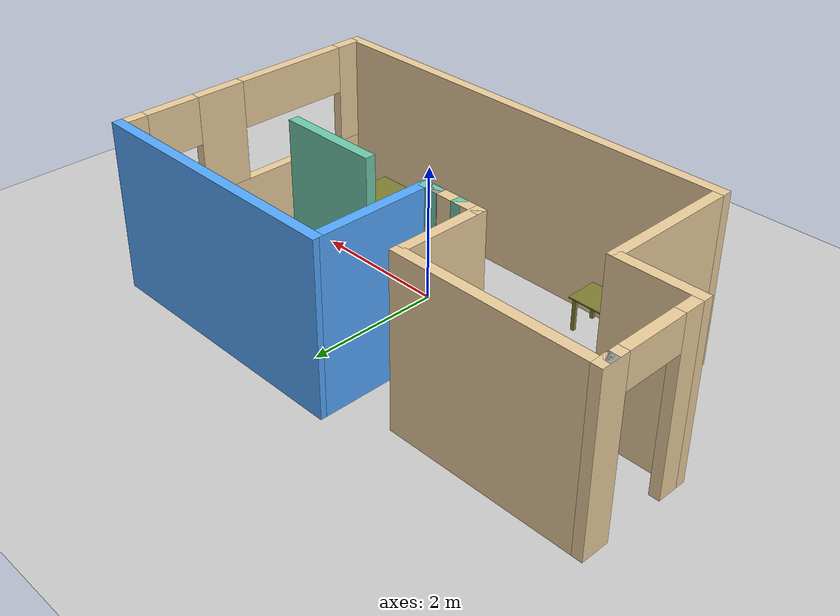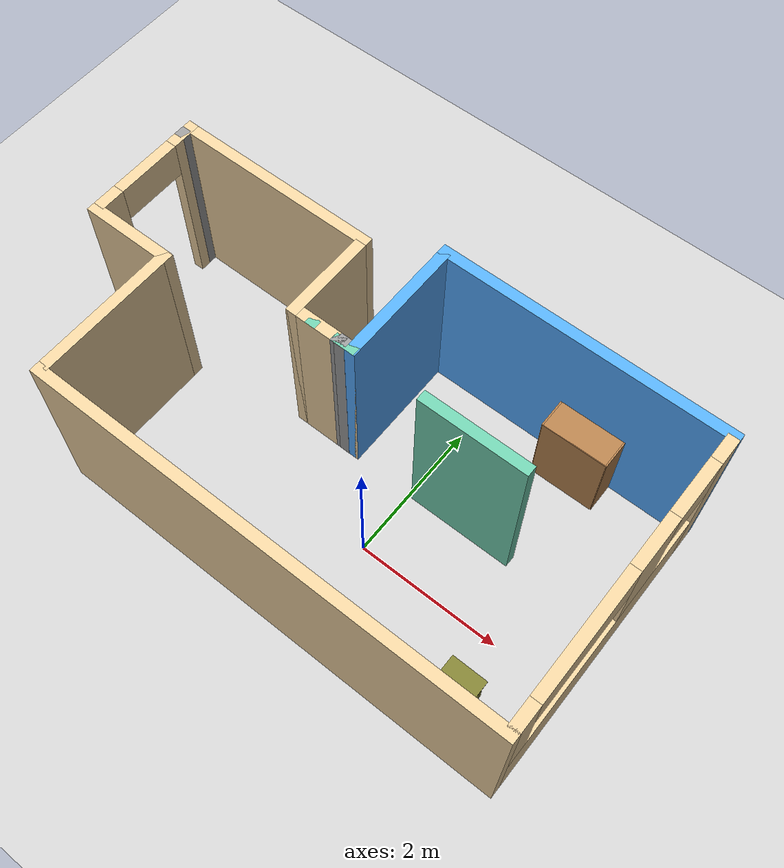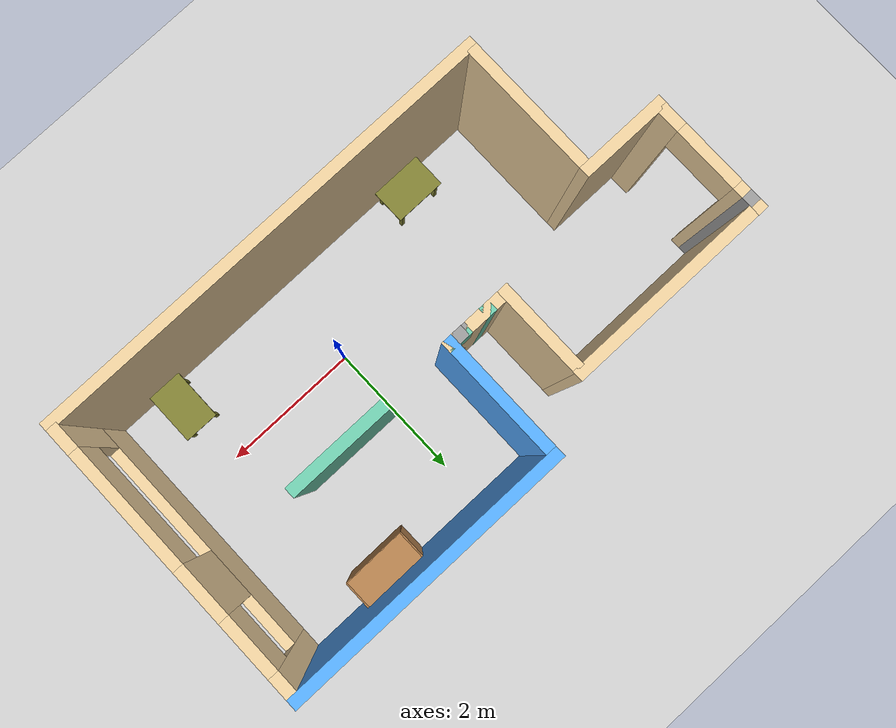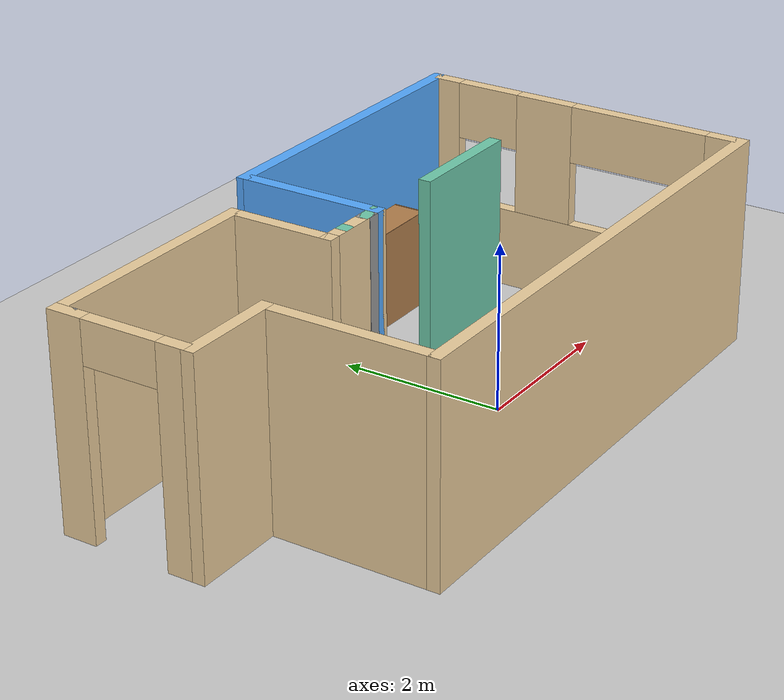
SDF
<sdf version="1.6">
 <world name="default">
  <plugin name="welcome_message" filename="libhello.so"/>
  <light name="sun" type="directional">
   <pose>0 0 10 0 -0 0</pose>
   <diffuse>0.8 0.8 0.8 1</diffuse>
   <specular>0.2 0.2 0.2 1</specular>
   <attenuation>
    <range>1000</range>
    <constant>0.9</constant>
    <linear>0.01</linear>
    <quadratic>0.001</quadratic>
   </attenuation>
   <direction>-0.5 0.1 -0.9</direction>
  </light>
  <model name="ground_plane">
   <static>1</static>
   <link name="link">
    <collision name="collision">
     <geometry><plane><normal>0 0 1</normal><size>100 100</size></plane></geometry>
     <surface>
      <contact><collide_bitmask>65535</collide_bitmask></contact>
      <friction><ode><mu>100</mu><mu2>50</mu2></ode></friction>
     </surface>
    </collision>
    <visual name="visual">
     <cast_shadows>0</cast_shadows>
     <geometry><plane><normal>0 0 1</normal><size>100 100</size></plane></geometry>
     <material>
      <script><uri>file://media/materials/scripts/gazebo.material</uri><name>Gazebo/Grey</name></script>
     </material>
    </visual>
   </link>
  </model>
  <gravity>0 0 -9.8</gravity>
  <magnetic_field>6e-06 2.3e-05 -4.2e-05</magnetic_field>
  <atmosphere type="adiabatic"/>
  <physics name="default_physics" default="0" type="ode">
   <max_step_size>0.001</max_step_size>
   <real_time_factor>1</real_time_factor>
   <real_time_update_rate>1000</real_time_update_rate>
  </physics>
  <scene><ambient>0.4 0.4 0.4 1</ambient><background>0.7 0.7 0.7 1</background><shadows>1</shadows></scene>
  <spherical_coordinates>
   <surface_model>EARTH_WGS84</surface_model>
   <latitude_deg>0</latitude_deg>
   <longitude_deg>0</longitude_deg>
   <elevation>0</elevation>
   <heading_deg>0</heading_deg>
  </spherical_coordinates>
  <model name="my_table">
   <link name="link_0">
    <pose>0.072072 -4.79324 0.208333 0 -0 0</pose>
    <inertial>
     <mass>1</mass>
     <inertia>
      <ixx>0.166667</ixx>
      <ixy>0</ixy>
      <ixz>0</ixz>
      <iyy>0.166667</iyy>
      <iyz>0</iyz>
      <izz>0.166667</izz>
     </inertia>
    </inertial>
    <visual name="visual">
     <geometry><box><size>0.5 0.75 0.02</size></box></geometry>
     <material>
      <lighting>1</lighting>
      <script><uri>file://media/materials/scripts/gazebo.material</uri><name>Gazebo/Grey</name></script>
      <shader type="pixel"><normal_map>__default__</normal_map></shader>
      <ambient>0.5 0.5 0.2 1</ambient>
      <diffuse>0.5 0.5 0.2 1</diffuse>
      <specular>0.01 0.01 0.01 1</specular>
      <emissive>0 0 0 1</emissive>
     </material>
    </visual>
    <collision name="collision">
     <geometry><box><size>0.5 0.75 0.02</size></box></geometry>
     <surface>
      <friction>
       <ode><mu>1</mu><mu2>1</mu2><fdir1>0 0 0</fdir1><slip1>0</slip1><slip2>0</slip2></ode>
       <torsional>
        <coefficient>1</coefficient>
        <patch_radius>0</patch_radius>
        <surface_radius>0</surface_radius>
        <use_patch_radius>1</use_patch_radius>
        <ode><slip>0</slip></ode>
       </torsional>
      </friction>
      <bounce><restitution_coefficient>0</restitution_coefficient><threshold>1e+06</threshold></bounce>
      <contact>
       <collide_without_contact>0</collide_without_contact>
       <collide_without_contact_bitmask>1</collide_without_contact_bitmask>
       <collide_bitmask>1</collide_bitmask>
       <ode>
        <soft_cfm>0</soft_cfm>
        <soft_erp>0.2</soft_erp>
        <kp>1e+13</kp>
        <kd>1</kd>
        <max_vel>0.01</max_vel>
        <min_depth>0</min_depth>
       </ode>
       <bullet>
        <split_impulse>1</split_impulse>
        <split_impulse_penetration_threshold>-0.01</split_impulse_penetration_threshold>
        <soft_cfm>0</soft_cfm>
        <soft_erp>0.2</soft_erp>
        <kp>1e+13</kp>
        <kd>1</kd>
       </bullet>
      </contact>
     </surface>
    </collision>
   </link>
   <link name="link_0_clone">
    <pose>0.272072 -4.49324 -0.041667 0 -0 0</pose>
    <inertial>
     <mass>1</mass>
     <inertia>
      <ixx>0.166667</ixx>
      <ixy>0</ixy>
      <ixz>0</ixz>
      <iyy>0.166667</iyy>
      <iyz>0</iyz>
      <izz>0.166667</izz>
     </inertia>
    </inertial>
    <visual name="visual">
     <geometry><box><size>0.05 0.05 0.49</size></box></geometry>
     <material>
      <lighting>1</lighting>
      <script><uri>file://media/materials/scripts/gazebo.material</uri><name>Gazebo/Grey</name></script>
      <shader type="pixel"><normal_map>__default__</normal_map></shader>
      <ambient>0.5 0.5 0.2 1</ambient>
      <diffuse>0.5 0.5 0.2 1</diffuse>
      <specular>0.01 0.01 0.01 1</specular>
      <emissive>0 0 0 1</emissive>
     </material>
    </visual>
    <collision name="collision">
     <geometry><box><size>0.05 0.05 0.49</size></box></geometry>
     <surface>
      <friction>
       <ode><mu>1</mu><mu2>1</mu2><fdir1>0 0 0</fdir1><slip1>0</slip1><slip2>0</slip2></ode>
       <torsional>
        <coefficient>1</coefficient>
        <patch_radius>0</patch_radius>
        <surface_radius>0</surface_radius>
        <use_patch_radius>1</use_patch_radius>
        <ode><slip>0</slip></ode>
       </torsional>
      </friction>
      <bounce><restitution_coefficient>0</restitution_coefficient><threshold>1e+06</threshold></bounce>
      <contact>
       <collide_without_contact>0</collide_without_contact>
       <collide_without_contact_bitmask>1</collide_without_contact_bitmask>
       <collide_bitmask>1</collide_bitmask>
       <ode>
        <soft_cfm>0</soft_cfm>
        <soft_erp>0.2</soft_erp>
        <kp>1e+13</kp>
        <kd>1</kd>
        <max_vel>0.01</max_vel>
        <min_depth>0</min_depth>
       </ode>
       <bullet>
        <split_impulse>1</split_impulse>
        <split_impulse_penetration_threshold>-0.01</split_impulse_penetration_threshold>
        <soft_cfm>0</soft_cfm>
        <soft_erp>0.2</soft_erp>
        <kp>1e+13</kp>
        <kd>1</kd>
       </bullet>
      </contact>
     </surface>
    </collision>
   </link>
   <link name="link_0_clone_clone_0">
    <pose>-0.127928 -4.49324 -0.041667 0 -0 0</pose>
    <inertial>
     <mass>1</mass>
     <inertia>
      <ixx>0.166667</ixx>
      <ixy>0</ixy>
      <ixz>0</ixz>
      <iyy>0.166667</iyy>
      <iyz>0</iyz>
      <izz>0.166667</izz>
     </inertia>
    </inertial>
    <visual name="visual">
     <geometry><box><size>0.05 0.05 0.49</size></box></geometry>
     <material>
      <lighting>1</lighting>
      <script><uri>file://media/materials/scripts/gazebo.material</uri><name>Gazebo/Grey</name></script>
      <shader type="pixel"><normal_map>__default__</normal_map></shader>
      <ambient>0.5 0.5 0.2 1</ambient>
      <diffuse>0.5 0.5 0.2 1</diffuse>
      <specular>0.01 0.01 0.01 1</specular>
      <emissive>0 0 0 1</emissive>
     </material>
    </visual>
    <collision name="collision">
     <geometry><box><size>0.05 0.05 0.49</size></box></geometry>
     <surface>
      <friction>
       <ode><mu>1</mu><mu2>1</mu2><fdir1>0 0 0</fdir1><slip1>0</slip1><slip2>0</slip2></ode>
       <torsional>
        <coefficient>1</coefficient>
        <patch_radius>0</patch_radius>
        <surface_radius>0</surface_radius>
        <use_patch_radius>1</use_patch_radius>
        <ode><slip>0</slip></ode>
       </torsional>
      </friction>
      <bounce><restitution_coefficient>0</restitution_coefficient><threshold>1e+06</threshold></bounce>
      <contact>
       <collide_without_contact>0</collide_without_contact>
       <collide_without_contact_bitmask>1</collide_without_contact_bitmask>
       <collide_bitmask>1</collide_bitmask>
       <ode>
        <soft_cfm>0</soft_cfm>
        <soft_erp>0.2</soft_erp>
        <kp>1e+13</kp>
        <kd>1</kd>
        <max_vel>0.01</max_vel>
        <min_depth>0</min_depth>
       </ode>
       <bullet>
        <split_impulse>1</split_impulse>
        <split_impulse_penetration_threshold>-0.01</split_impulse_penetration_threshold>
        <soft_cfm>0</soft_cfm>
        <soft_erp>0.2</soft_erp>
        <kp>1e+13</kp>
        <kd>1</kd>
       </bullet>
      </contact>
     </surface>
    </collision>
   </link>
   <link name="link_0_clone_clone_1">
    <pose>0.272072 -5.09324 -0.041667 0 -0 0</pose>
    <inertial>
     <mass>1</mass>
     <inertia>
      <ixx>0.166667</ixx>
      <ixy>0</ixy>
      <ixz>0</ixz>
      <iyy>0.166667</iyy>
      <iyz>0</iyz>
      <izz>0.166667</izz>
     </inertia>
    </inertial>
    <visual name="visual">
     <geometry><box><size>0.05 0.05 0.49</size></box></geometry>
     <material>
      <lighting>1</lighting>
      <script><uri>file://media/materials/scripts/gazebo.material</uri><name>Gazebo/Grey</name></script>
      <shader type="pixel"><normal_map>__default__</normal_map></shader>
      <ambient>0.5 0.5 0.2 1</ambient>
      <diffuse>0.5 0.5 0.2 1</diffuse>
      <specular>0.01 0.01 0.01 1</specular>
      <emissive>0 0 0 1</emissive>
     </material>
    </visual>
    <collision name="collision">
     <geometry><box><size>0.05 0.05 0.49</size></box></geometry>
     <surface>
      <friction>
       <ode><mu>1</mu><mu2>1</mu2><fdir1>0 0 0</fdir1><slip1>0</slip1><slip2>0</slip2></ode>
       <torsional>
        <coefficient>1</coefficient>
        <patch_radius>0</patch_radius>
        <surface_radius>0</surface_radius>
        <use_patch_radius>1</use_patch_radius>
        <ode><slip>0</slip></ode>
       </torsional>
      </friction>
      <bounce><restitution_coefficient>0</restitution_coefficient><threshold>1e+06</threshold></bounce>
      <contact>
       <collide_without_contact>0</collide_without_contact>
       <collide_without_contact_bitmask>1</collide_without_contact_bitmask>
       <collide_bitmask>1</collide_bitmask>
       <ode>
        <soft_cfm>0</soft_cfm>
        <soft_erp>0.2</soft_erp>
        <kp>1e+13</kp>
        <kd>1</kd>
        <max_vel>0.01</max_vel>
        <min_depth>0</min_depth>
       </ode>
       <bullet>
        <split_impulse>1</split_impulse>
        <split_impulse_penetration_threshold>-0.01</split_impulse_penetration_threshold>
        <soft_cfm>0</soft_cfm>
        <soft_erp>0.2</soft_erp>
        <kp>1e+13</kp>
        <kd>1</kd>
       </bullet>
      </contact>
     </surface>
    </collision>
   </link>
   <link name="link_0_clone_clone_2">
    <pose>-0.127928 -5.09324 -0.041667 0 -0 0</pose>
    <inertial>
     <mass>1</mass>
     <inertia>
      <ixx>0.166667</ixx>
      <ixy>0</ixy>
      <ixz>0</ixz>
      <iyy>0.166667</iyy>
      <iyz>0</iyz>
      <izz>0.166667</izz>
     </inertia>
    </inertial>
    <visual name="visual">
     <geometry><box><size>0.05 0.05 0.49</size></box></geometry>
     <material>
      <lighting>1</lighting>
      <script><uri>file://media/materials/scripts/gazebo.material</uri><name>Gazebo/Grey</name></script>
      <shader type="pixel"><normal_map>__default__</normal_map></shader>
      <ambient>0.5 0.5 0.2 1</ambient>
      <diffuse>0.5 0.5 0.2 1</diffuse>
      <specular>0.01 0.01 0.01 1</specular>
      <emissive>0 0 0 1</emissive>
     </material>
    </visual>
    <collision name="collision">
     <geometry><box><size>0.05 0.05 0.49</size></box></geometry>
     <surface>
      <friction>
       <ode><mu>1</mu><mu2>1</mu2><fdir1>0 0 0</fdir1><slip1>0</slip1><slip2>0</slip2></ode>
       <torsional>
        <coefficient>1</coefficient>
        <patch_radius>0</patch_radius>
        <surface_radius>0</surface_radius>
        <use_patch_radius>1</use_patch_radius>
        <ode><slip>0</slip></ode>
       </torsional>
      </friction>
      <bounce><restitution_coefficient>0</restitution_coefficient><threshold>1e+06</threshold></bounce>
      <contact>
       <collide_without_contact>0</collide_without_contact>
       <collide_without_contact_bitmask>1</collide_without_contact_bitmask>
       <collide_bitmask>1</collide_bitmask>
       <ode>
        <soft_cfm>0</soft_cfm>
        <soft_erp>0.2</soft_erp>
        <kp>1e+13</kp>
        <kd>1</kd>
        <max_vel>0.01</max_vel>
        <min_depth>0</min_depth>
       </ode>
       <bullet>
        <split_impulse>1</split_impulse>
        <split_impulse_penetration_threshold>-0.01</split_impulse_penetration_threshold>
        <soft_cfm>0</soft_cfm>
        <soft_erp>0.2</soft_erp>
        <kp>1e+13</kp>
        <kd>1</kd>
       </bullet>
      </contact>
     </surface>
    </collision>
   </link>
   <joint name="link_0_JOINT_4" type="fixed">
    <parent>link_0</parent>
    <child>link_0_clone</child>
    <physics>
     <ode><limit><cfm>0</cfm><erp>0.2</erp></limit><suspension><cfm>0</cfm><erp>0.2</erp></suspension></ode>
    </physics>
   </joint>
   <joint name="link_0_JOINT_5" type="fixed">
    <parent>link_0</parent>
    <child>link_0_clone_clone_0</child>
    <physics>
     <ode><limit><cfm>0</cfm><erp>0.2</erp></limit><suspension><cfm>0</cfm><erp>0.2</erp></suspension></ode>
    </physics>
   </joint>
   <joint name="link_0_JOINT_6" type="fixed">
    <parent>link_0</parent>
    <child>link_0_clone_clone_1</child>
    <physics>
     <ode><limit><cfm>0</cfm><erp>0.2</erp></limit><suspension><cfm>0</cfm><erp>0.2</erp></suspension></ode>
    </physics>
   </joint>
   <joint name="link_0_JOINT_7" type="fixed">
    <parent>link_0</parent>
    <child>link_0_clone_clone_2</child>
    <physics>
     <ode><limit><cfm>0</cfm><erp>0.2</erp></limit><suspension><cfm>0</cfm><erp>0.2</erp></suspension></ode>
    </physics>
   </joint>
   <static>0</static>
   <pose>-6.94534 -1.12949 0.286655 -2e-06 -0 1.57271</pose>
  </model>
  <model name="my_table_clone_0">
   <link name="link_0">
    <pose>0.072072 -4.79324 0.208333 0 -0 0</pose>
    <inertial>
     <mass>1</mass>
     <inertia>
      <ixx>0.166667</ixx>
      <ixy>0</ixy>
      <ixz>0</ixz>
      <iyy>0.166667</iyy>
      <iyz>0</iyz>
      <izz>0.166667</izz>
     </inertia>
    </inertial>
    <visual name="visual">
     <geometry><box><size>0.5 0.75 0.02</size></box></geometry>
     <material>
      <lighting>1</lighting>
      <script><uri>file://media/materials/scripts/gazebo.material</uri><name>Gazebo/Grey</name></script>
      <shader type="pixel"><normal_map>__default__</normal_map></shader>
      <ambient>0.5 0.5 0.2 1</ambient>
      <diffuse>0.5 0.5 0.2 1</diffuse>
      <specular>0.01 0.01 0.01 1</specular>
      <emissive>0 0 0 1</emissive>
     </material>
    </visual>
    <collision name="collision">
     <geometry><box><size>0.5 0.75 0.02</size></box></geometry>
     <surface>
      <friction>
       <ode><mu>1</mu><mu2>1</mu2><fdir1>0 0 0</fdir1><slip1>0</slip1><slip2>0</slip2></ode>
       <torsional>
        <coefficient>1</coefficient>
        <patch_radius>0</patch_radius>
        <surface_radius>0</surface_radius>
        <use_patch_radius>1</use_patch_radius>
        <ode><slip>0</slip></ode>
       </torsional>
      </friction>
      <bounce><restitution_coefficient>0</restitution_coefficient><threshold>1e+06</threshold></bounce>
      <contact>
       <collide_without_contact>0</collide_without_contact>
       <collide_without_contact_bitmask>1</collide_without_contact_bitmask>
       <collide_bitmask>1</collide_bitmask>
       <ode>
        <soft_cfm>0</soft_cfm>
        <soft_erp>0.2</soft_erp>
        <kp>1e+13</kp>
        <kd>1</kd>
        <max_vel>0.01</max_vel>
        <min_depth>0</min_depth>
       </ode>
       <bullet>
        <split_impulse>1</split_impulse>
        <split_impulse_penetration_threshold>-0.01</split_impulse_penetration_threshold>
        <soft_cfm>0</soft_cfm>
        <soft_erp>0.2</soft_erp>
        <kp>1e+13</kp>
        <kd>1</kd>
       </bullet>
      </contact>
     </surface>
    </collision>
   </link>
   <link name="link_0_clone">
    <pose>0.272072 -4.49324 -0.041667 0 -0 0</pose>
    <inertial>
     <mass>1</mass>
     <inertia>
      <ixx>0.166667</ixx>
      <ixy>0</ixy>
      <ixz>0</ixz>
      <iyy>0.166667</iyy>
      <iyz>0</iyz>
      <izz>0.166667</izz>
     </inertia>
    </inertial>
    <visual name="visual">
     <geometry><box><size>0.05 0.05 0.49</size></box></geometry>
     <material>
      <lighting>1</lighting>
      <script><uri>file://media/materials/scripts/gazebo.material</uri><name>Gazebo/Grey</name></script>
      <shader type="pixel"><normal_map>__default__</normal_map></shader>
      <ambient>0.5 0.5 0.2 1</ambient>
      <diffuse>0.5 0.5 0.2 1</diffuse>
      <specular>0.01 0.01 0.01 1</specular>
      <emissive>0 0 0 1</emissive>
     </material>
    </visual>
    <collision name="collision">
     <geometry><box><size>0.05 0.05 0.49</size></box></geometry>
     <surface>
      <friction>
       <ode><mu>1</mu><mu2>1</mu2><fdir1>0 0 0</fdir1><slip1>0</slip1><slip2>0</slip2></ode>
       <torsional>
        <coefficient>1</coefficient>
        <patch_radius>0</patch_radius>
        <surface_radius>0</surface_radius>
        <use_patch_radius>1</use_patch_radius>
        <ode><slip>0</slip></ode>
       </torsional>
      </friction>
      <bounce><restitution_coefficient>0</restitution_coefficient><threshold>1e+06</threshold></bounce>
      <contact>
       <collide_without_contact>0</collide_without_contact>
       <collide_without_contact_bitmask>1</collide_without_contact_bitmask>
       <collide_bitmask>1</collide_bitmask>
       <ode>
        <soft_cfm>0</soft_cfm>
        <soft_erp>0.2</soft_erp>
        <kp>1e+13</kp>
        <kd>1</kd>
        <max_vel>0.01</max_vel>
        <min_depth>0</min_depth>
       </ode>
       <bullet>
        <split_impulse>1</split_impulse>
        <split_impulse_penetration_threshold>-0.01</split_impulse_penetration_threshold>
        <soft_cfm>0</soft_cfm>
        <soft_erp>0.2</soft_erp>
        <kp>1e+13</kp>
        <kd>1</kd>
       </bullet>
      </contact>
     </surface>
    </collision>
   </link>
   <link name="link_0_clone_clone_0">
    <pose>-0.127928 -4.49324 -0.041667 0 -0 0</pose>
    <inertial>
     <mass>1</mass>
     <inertia>
      <ixx>0.166667</ixx>
      <ixy>0</ixy>
      <ixz>0</ixz>
      <iyy>0.166667</iyy>
      <iyz>0</iyz>
      <izz>0.166667</izz>
     </inertia>
    </inertial>
    <visual name="visual">
     <geometry><box><size>0.05 0.05 0.49</size></box></geometry>
     <material>
      <lighting>1</lighting>
      <script><uri>file://media/materials/scripts/gazebo.material</uri><name>Gazebo/Grey</name></script>
      <shader type="pixel"><normal_map>__default__</normal_map></shader>
      <ambient>0.5 0.5 0.2 1</ambient>
      <diffuse>0.5 0.5 0.2 1</diffuse>
      <specular>0.01 0.01 0.01 1</specular>
      <emissive>0 0 0 1</emissive>
     </material>
    </visual>
    <collision name="collision">
     <geometry><box><size>0.05 0.05 0.49</size></box></geometry>
     <surface>
      <friction>
       <ode><mu>1</mu><mu2>1</mu2><fdir1>0 0 0</fdir1><slip1>0</slip1><slip2>0</slip2></ode>
       <torsional>
        <coefficient>1</coefficient>
        <patch_radius>0</patch_radius>
        <surface_radius>0</surface_radius>
        <use_patch_radius>1</use_patch_radius>
        <ode><slip>0</slip></ode>
       </torsional>
      </friction>
      <bounce><restitution_coefficient>0</restitution_coefficient><threshold>1e+06</threshold></bounce>
      <contact>
       <collide_without_contact>0</collide_without_contact>
       <collide_without_contact_bitmask>1</collide_without_contact_bitmask>
       <collide_bitmask>1</collide_bitmask>
       <ode>
        <soft_cfm>0</soft_cfm>
        <soft_erp>0.2</soft_erp>
        <kp>1e+13</kp>
        <kd>1</kd>
        <max_vel>0.01</max_vel>
        <min_depth>0</min_depth>
       </ode>
       <bullet>
        <split_impulse>1</split_impulse>
        <split_impulse_penetration_threshold>-0.01</split_impulse_penetration_threshold>
        <soft_cfm>0</soft_cfm>
        <soft_erp>0.2</soft_erp>
        <kp>1e+13</kp>
        <kd>1</kd>
       </bullet>
      </contact>
     </surface>
    </collision>
   </link>
   <link name="link_0_clone_clone_1">
    <pose>0.272072 -5.09324 -0.041667 0 -0 0</pose>
    <inertial>
     <mass>1</mass>
     <inertia>
      <ixx>0.166667</ixx>
      <ixy>0</ixy>
      <ixz>0</ixz>
      <iyy>0.166667</iyy>
      <iyz>0</iyz>
      <izz>0.166667</izz>
     </inertia>
    </inertial>
    <visual name="visual">
     <geometry><box><size>0.05 0.05 0.49</size></box></geometry>
     <material>
      <lighting>1</lighting>
      <script><uri>file://media/materials/scripts/gazebo.material</uri><name>Gazebo/Grey</name></script>
      <shader type="pixel"><normal_map>__default__</normal_map></shader>
      <ambient>0.5 0.5 0.2 1</ambient>
      <diffuse>0.5 0.5 0.2 1</diffuse>
      <specular>0.01 0.01 0.01 1</specular>
      <emissive>0 0 0 1</emissive>
     </material>
    </visual>
    <collision name="collision">
     <geometry><box><size>0.05 0.05 0.49</size></box></geometry>
     <surface>
      <friction>
       <ode><mu>1</mu><mu2>1</mu2><fdir1>0 0 0</fdir1><slip1>0</slip1><slip2>0</slip2></ode>
       <torsional>
        <coefficient>1</coefficient>
        <patch_radius>0</patch_radius>
        <surface_radius>0</surface_radius>
        <use_patch_radius>1</use_patch_radius>
        <ode><slip>0</slip></ode>
       </torsional>
      </friction>
      <bounce><restitution_coefficient>0</restitution_coefficient><threshold>1e+06</threshold></bounce>
      <contact>
       <collide_without_contact>0</collide_without_contact>
       <collide_without_contact_bitmask>1</collide_without_contact_bitmask>
       <collide_bitmask>1</collide_bitmask>
       <ode>
        <soft_cfm>0</soft_cfm>
        <soft_erp>0.2</soft_erp>
        <kp>1e+13</kp>
        <kd>1</kd>
        <max_vel>0.01</max_vel>
        <min_depth>0</min_depth>
       </ode>
       <bullet>
        <split_impulse>1</split_impulse>
        <split_impulse_penetration_threshold>-0.01</split_impulse_penetration_threshold>
        <soft_cfm>0</soft_cfm>
        <soft_erp>0.2</soft_erp>
        <kp>1e+13</kp>
        <kd>1</kd>
       </bullet>
      </contact>
     </surface>
    </collision>
   </link>
   <link name="link_0_clone_clone_2">
    <pose>-0.127928 -5.09324 -0.041667 0 -0 0</pose>
    <inertial>
     <mass>1</mass>
     <inertia>
      <ixx>0.166667</ixx>
      <ixy>0</ixy>
      <ixz>0</ixz>
      <iyy>0.166667</iyy>
      <iyz>0</iyz>
      <izz>0.166667</izz>
     </inertia>
    </inertial>
    <visual name="visual">
     <geometry><box><size>0.05 0.05 0.49</size></box></geometry>
     <material>
      <lighting>1</lighting>
      <script><uri>file://media/materials/scripts/gazebo.material</uri><name>Gazebo/Grey</name></script>
      <shader type="pixel"><normal_map>__default__</normal_map></shader>
      <ambient>0.5 0.5 0.2 1</ambient>
      <diffuse>0.5 0.5 0.2 1</diffuse>
      <specular>0.01 0.01 0.01 1</specular>
      <emissive>0 0 0 1</emissive>
     </material>
    </visual>
    <collision name="collision">
     <geometry><box><size>0.05 0.05 0.49</size></box></geometry>
     <surface>
      <friction>
       <ode><mu>1</mu><mu2>1</mu2><fdir1>0 0 0</fdir1><slip1>0</slip1><slip2>0</slip2></ode>
       <torsional>
        <coefficient>1</coefficient>
        <patch_radius>0</patch_radius>
        <surface_radius>0</surface_radius>
        <use_patch_radius>1</use_patch_radius>
        <ode><slip>0</slip></ode>
       </torsional>
      </friction>
      <bounce><restitution_coefficient>0</restitution_coefficient><threshold>1e+06</threshold></bounce>
      <contact>
       <collide_without_contact>0</collide_without_contact>
       <collide_without_contact_bitmask>1</collide_without_contact_bitmask>
       <collide_bitmask>1</collide_bitmask>
       <ode>
        <soft_cfm>0</soft_cfm>
        <soft_erp>0.2</soft_erp>
        <kp>1e+13</kp>
        <kd>1</kd>
        <max_vel>0.01</max_vel>
        <min_depth>0</min_depth>
       </ode>
       <bullet>
        <split_impulse>1</split_impulse>
        <split_impulse_penetration_threshold>-0.01</split_impulse_penetration_threshold>
        <soft_cfm>0</soft_cfm>
        <soft_erp>0.2</soft_erp>
        <kp>1e+13</kp>
        <kd>1</kd>
       </bullet>
      </contact>
     </surface>
    </collision>
   </link>
   <joint name="link_0_JOINT_4" type="fixed">
    <parent>link_0</parent>
    <child>link_0_clone</child>
    <physics>
     <ode><limit><cfm>0</cfm><erp>0.2</erp></limit><suspension><cfm>0</cfm><erp>0.2</erp></suspension></ode>
    </physics>
   </joint>
   <joint name="link_0_JOINT_5" type="fixed">
    <parent>link_0</parent>
    <child>link_0_clone_clone_0</child>
    <physics>
     <ode><limit><cfm>0</cfm><erp>0.2</erp></limit><suspension><cfm>0</cfm><erp>0.2</erp></suspension></ode>
    </physics>
   </joint>
   <joint name="link_0_JOINT_6" type="fixed">
    <parent>link_0</parent>
    <child>link_0_clone_clone_1</child>
    <physics>
     <ode><limit><cfm>0</cfm><erp>0.2</erp></limit><suspension><cfm>0</cfm><erp>0.2</erp></suspension></ode>
    </physics>
   </joint>
   <joint name="link_0_JOINT_7" type="fixed">
    <parent>link_0</parent>
    <child>link_0_clone_clone_2</child>
    <physics>
     <ode><limit><cfm>0</cfm><erp>0.2</erp></limit><suspension><cfm>0</cfm><erp>0.2</erp></suspension></ode>
    </physics>
   </joint>
   <static>0</static>
   <pose>1.9531 3.87664 0.286666 0 -2e-06 -0.004011</pose>
  </model>
  <model name="bookshelf">
   <static>1</static>
   <link name="link">
    <inertial><mass>1</mass></inertial>
    <collision name="back">
     <pose>0 0.005 0.6 0 -0 0</pose>
     <geometry><box><size>0.9 0.01 1.2</size></box></geometry>
    </collision>
    <visual name="visual1">
     <pose>0 0.005 0.6 0 -0 0</pose>
     <geometry><box><size>0.9 0.01 1.2</size></box></geometry>
     <material>
      <script><uri>file://media/materials/scripts/gazebo.material</uri><name>Gazebo/Wood</name></script>
     </material>
    </visual>
    <collision name="left_side">
     <pose>0.45 -0.195 0.6 0 -0 0</pose>
     <geometry><box><size>0.02 0.4 1.2</size></box></geometry>
    </collision>
    <visual name="visual2">
     <pose>0.45 -0.195 0.6 0 -0 0</pose>
     <geometry><box><size>0.02 0.4 1.2</size></box></geometry>
     <material>
      <script><uri>file://media/materials/scripts/gazebo.material</uri><name>Gazebo/Wood</name></script>
     </material>
    </visual>
    <collision name="right_side">
     <pose>-0.45 -0.195 0.6 0 -0 0</pose>
     <geometry><box><size>0.02 0.4 1.2</size></box></geometry>
    </collision>
    <visual name="visual3">
     <pose>-0.45 -0.195 0.6 0 -0 0</pose>
     <geometry><box><size>0.02 0.4 1.2</size></box></geometry>
     <material>
      <script><uri>file://media/materials/scripts/gazebo.material</uri><name>Gazebo/Wood</name></script>
     </material>
    </visual>
    <collision name="bottom">
     <pose>0 -0.195 0.03 0 -0 0</pose>
     <geometry><box><size>0.88 0.4 0.06</size></box></geometry>
    </collision>
    <visual name="visual4">
     <pose>0 -0.195 0.03 0 -0 0</pose>
     <geometry><box><size>0.88 0.4 0.06</size></box></geometry>
     <material>
      <script><uri>file://media/materials/scripts/gazebo.material</uri><name>Gazebo/Wood</name></script>
     </material>
    </visual>
    <collision name="top">
     <pose>0 -0.195 1.19 0 -0 0</pose>
     <geometry><box><size>0.88 0.4 0.02</size></box></geometry>
    </collision>
    <visual name="visual5">
     <pose>0 -0.195 1.19 0 -0 0</pose>
     <geometry><box><size>0.88 0.4 0.02</size></box></geometry>
     <material>
      <script><uri>file://media/materials/scripts/gazebo.material</uri><name>Gazebo/Wood</name></script>
     </material>
    </visual>
    <collision name="low_shelf">
     <pose>0 -0.195 0.43 0 -0 0</pose>
     <geometry><box><size>0.88 0.4 0.02</size></box></geometry>
    </collision>
    <visual name="visual6">
     <pose>0 -0.195 0.43 0 -0 0</pose>
     <geometry><box><size>0.88 0.4 0.02</size></box></geometry>
     <material>
      <script><uri>file://media/materials/scripts/gazebo.material</uri><name>Gazebo/Wood</name></script>
     </material>
    </visual>
    <collision name="high_shelf">
     <pose>0 -0.195 0.8 0 -0 0</pose>
     <geometry><box><size>0.88 0.4 0.02</size></box></geometry>
    </collision>
    <visual name="visual7">
     <pose>0 -0.195 0.8 0 -0 0</pose>
     <geometry><box><size>0.88 0.4 0.02</size></box></geometry>
     <material>
      <script><uri>file://media/materials/scripts/gazebo.material</uri><name>Gazebo/Wood</name></script>
     </material>
    </visual>
   </link>
   <pose>1.43287 2.19209 0 0 0 -3.13572</pose>
  </model>
  <model name="my_building">
   <link name="Wall_0">
    <pose>-2.275 1.54483 0 0 -0 0</pose>
    <visual name="Wall_0_Visual">
     <pose>0 0 1.25 0 -0 0</pose>
     <geometry><box><size>2.75 0.15 2.5</size></box></geometry>
     <material>
      <script><uri>file://media/materials/scripts/gazebo.material</uri><name>Gazebo/Grey</name></script>
      <ambient>0.921569 0.807843 0.615686 1</ambient>
      <shader type="pixel"/>
      <diffuse>0.7 0.7 0.7 1</diffuse>
      <specular>0.01 0.01 0.01 1</specular>
      <emissive>0 0 0 1</emissive>
     </material>
     <meta><layer>0</layer></meta>
    </visual>
    <collision name="Wall_0_Collision">
     <pose>0 0 1.25 0 -0 0</pose>
     <geometry><box><size>2.75 0.15 2.5</size></box></geometry>
     <surface>
      <friction>
       <ode><mu>1</mu><mu2>1</mu2><fdir1>0 0 0</fdir1><slip1>0</slip1><slip2>0</slip2></ode>
       <torsional>
        <coefficient>1</coefficient>
        <patch_radius>0</patch_radius>
        <surface_radius>0</surface_radius>
        <use_patch_radius>1</use_patch_radius>
        <ode><slip>0</slip></ode>
       </torsional>
      </friction>
      <bounce><restitution_coefficient>0</restitution_coefficient><threshold>1e+06</threshold></bounce>
      <contact>
       <collide_without_contact>0</collide_without_contact>
       <collide_without_contact_bitmask>1</collide_without_contact_bitmask>
       <collide_bitmask>1</collide_bitmask>
       <ode>
        <soft_cfm>0</soft_cfm>
        <soft_erp>0.2</soft_erp>
        <kp>1e+13</kp>
        <kd>1</kd>
        <max_vel>0.01</max_vel>
        <min_depth>0</min_depth>
       </ode>
       <bullet>
        <split_impulse>1</split_impulse>
        <split_impulse_penetration_threshold>-0.01</split_impulse_penetration_threshold>
        <soft_cfm>0</soft_cfm>
        <soft_erp>0.2</soft_erp>
        <kp>1e+13</kp>
        <kd>1</kd>
       </bullet>
      </contact>
     </surface>
    </collision>
   </link>
   <link name="Wall_1">
    <pose>-0.975 0.875 0 0 0 -1.5708</pose>
    <visual name="Wall_1_Visual">
     <pose>0 0 1.25 0 -0 0</pose>
     <geometry><box><size>1.25 0.15 2.5</size></box></geometry>
     <material>
      <script><uri>file://media/materials/scripts/gazebo.material</uri><name>Gazebo/Grey</name></script>
      <ambient>0.921569 0.807843 0.615686 1</ambient>
      <shader type="pixel"/>
      <diffuse>0.7 0.7 0.7 1</diffuse>
      <specular>0.01 0.01 0.01 1</specular>
      <emissive>0 0 0 1</emissive>
     </material>
     <meta><layer>0</layer></meta>
    </visual>
    <collision name="Wall_1_Collision">
     <pose>0 0 1.25 0 -0 0</pose>
     <geometry><box><size>1.25 0.15 2.5</size></box></geometry>
     <surface>
      <friction>
       <ode><mu>1</mu><mu2>1</mu2><fdir1>0 0 0</fdir1><slip1>0</slip1><slip2>0</slip2></ode>
       <torsional>
        <coefficient>1</coefficient>
        <patch_radius>0</patch_radius>
        <surface_radius>0</surface_radius>
        <use_patch_radius>1</use_patch_radius>
        <ode><slip>0</slip></ode>
       </torsional>
      </friction>
      <bounce><restitution_coefficient>0</restitution_coefficient><threshold>1e+06</threshold></bounce>
      <contact>
       <collide_without_contact>0</collide_without_contact>
       <collide_without_contact_bitmask>1</collide_without_contact_bitmask>
       <collide_bitmask>1</collide_bitmask>
       <ode>
        <soft_cfm>0</soft_cfm>
        <soft_erp>0.2</soft_erp>
        <kp>1e+13</kp>
        <kd>1</kd>
        <max_vel>0.01</max_vel>
        <min_depth>0</min_depth>
       </ode>
       <bullet>
        <split_impulse>1</split_impulse>
        <split_impulse_penetration_threshold>-0.01</split_impulse_penetration_threshold>
        <soft_cfm>0</soft_cfm>
        <soft_erp>0.2</soft_erp>
        <kp>1e+13</kp>
        <kd>1</kd>
       </bullet>
      </contact>
     </surface>
    </collision>
   </link>
   <link name="Wall_10">
    <pose>-3.725 1.425 0 0 -0 0</pose>
    <visual name="Wall_10_Visual">
     <pose>0 0 1.25 0 -0 0</pose>
     <geometry><box><size>0.15 0.15 2.5</size></box></geometry>
     <material>
      <script><uri>file://media/materials/scripts/gazebo.material</uri><name>Gazebo/Grey</name></script>
      <ambient>1 1 1 1</ambient>
      <shader type="pixel"/>
      <diffuse>0.7 0.7 0.7 1</diffuse>
      <specular>0.01 0.01 0.01 1</specular>
      <emissive>0 0 0 1</emissive>
     </material>
     <meta><layer>0</layer></meta>
    </visual>
    <collision name="Wall_10_Collision">
     <pose>0 0 1.25 0 -0 0</pose>
     <geometry><box><size>0.15 0.15 2.5</size></box></geometry>
     <surface>
      <friction>
       <ode><mu>1</mu><mu2>1</mu2><fdir1>0 0 0</fdir1><slip1>0</slip1><slip2>0</slip2></ode>
       <torsional>
        <coefficient>1</coefficient>
        <patch_radius>0</patch_radius>
        <surface_radius>0</surface_radius>
        <use_patch_radius>1</use_patch_radius>
        <ode><slip>0</slip></ode>
       </torsional>
      </friction>
      <bounce><restitution_coefficient>0</restitution_coefficient><threshold>1e+06</threshold></bounce>
      <contact>
       <collide_without_contact>0</collide_without_contact>
       <collide_without_contact_bitmask>1</collide_without_contact_bitmask>
       <collide_bitmask>1</collide_bitmask>
       <ode>
        <soft_cfm>0</soft_cfm>
        <soft_erp>0.2</soft_erp>
        <kp>1e+13</kp>
        <kd>1</kd>
        <max_vel>0.01</max_vel>
        <min_depth>0</min_depth>
       </ode>
       <bullet>
        <split_impulse>1</split_impulse>
        <split_impulse_penetration_threshold>-0.01</split_impulse_penetration_threshold>
        <soft_cfm>0</soft_cfm>
        <soft_erp>0.2</soft_erp>
        <kp>1e+13</kp>
        <kd>1</kd>
       </bullet>
      </contact>
     </surface>
    </collision>
   </link>
   <link name="Wall_12">
    <pose>-3.725 0.796381 0 0 -0 1.5708</pose>
    <visual name="Wall_12_Visual_0">
     <pose>-0.658151 0 1.25 0 -0 0</pose>
     <geometry><box><size>0.333697 0.15 2.5</size></box></geometry>
     <material>
      <script><uri>file://media/materials/scripts/gazebo.material</uri><name>Gazebo/Grey</name></script>
      <ambient>0.921569 0.807843 0.615686 1</ambient>
      <shader type="pixel"/>
      <diffuse>0.7 0.7 0.7 1</diffuse>
      <specular>0.01 0.01 0.01 1</specular>
      <emissive>0 0 0 1</emissive>
     </material>
     <meta><layer>0</layer></meta>
    </visual>
    <visual name="Wall_12_Visual_1">
     <pose>0.616849 0 1.25 0 -0 0</pose>
     <geometry><box><size>0.416303 0.15 2.5</size></box></geometry>
     <material>
      <script><uri>file://media/materials/scripts/gazebo.material</uri><name>Gazebo/Grey</name></script>
      <ambient>0.921569 0.807843 0.615686 1</ambient>
      <shader type="pixel"/>
      <diffuse>0.7 0.7 0.7 1</diffuse>
      <specular>0.01 0.01 0.01 1</specular>
      <emissive>0 0 0 1</emissive>
     </material>
     <meta><layer>0</layer></meta>
    </visual>
    <visual name="Wall_12_Visual_2">
     <pose>-0.041303 0 2.25 0 -0 0</pose>
     <geometry><box><size>0.9 0.15 0.5</size></box></geometry>
     <material>
      <script><uri>file://media/materials/scripts/gazebo.material</uri><name>Gazebo/Grey</name></script>
      <ambient>0.921569 0.807843 0.615686 1</ambient>
      <shader type="pixel"/>
      <diffuse>0.7 0.7 0.7 1</diffuse>
      <specular>0.01 0.01 0.01 1</specular>
      <emissive>0 0 0 1</emissive>
     </material>
     <meta><layer>0</layer></meta>
    </visual>
    <collision name="Wall_12_Collision_0">
     <pose>-0.658151 0 1.25 0 -0 0</pose>
     <geometry><box><size>0.333697 0.15 2.5</size></box></geometry>
     <surface>
      <friction>
       <ode><mu>1</mu><mu2>1</mu2><fdir1>0 0 0</fdir1><slip1>0</slip1><slip2>0</slip2></ode>
       <torsional>
        <coefficient>1</coefficient>
        <patch_radius>0</patch_radius>
        <surface_radius>0</surface_radius>
        <use_patch_radius>1</use_patch_radius>
        <ode><slip>0</slip></ode>
       </torsional>
      </friction>
      <bounce><restitution_coefficient>0</restitution_coefficient><threshold>1e+06</threshold></bounce>
      <contact>
       <collide_without_contact>0</collide_without_contact>
       <collide_without_contact_bitmask>1</collide_without_contact_bitmask>
       <collide_bitmask>1</collide_bitmask>
       <ode>
        <soft_cfm>0</soft_cfm>
        <soft_erp>0.2</soft_erp>
        <kp>1e+13</kp>
        <kd>1</kd>
        <max_vel>0.01</max_vel>
        <min_depth>0</min_depth>
       </ode>
       <bullet>
        <split_impulse>1</split_impulse>
        <split_impulse_penetration_threshold>-0.01</split_impulse_penetration_threshold>
        <soft_cfm>0</soft_cfm>
        <soft_erp>0.2</soft_erp>
        <kp>1e+13</kp>
        <kd>1</kd>
       </bullet>
      </contact>
     </surface>
    </collision>
    <collision name="Wall_12_Collision_2">
     <pose>-0.041303 0 2.25 0 -0 0</pose>
     <geometry><box><size>0.9 0.15 0.5</size></box></geometry>
     <surface>
      <friction>
       <ode><mu>1</mu><mu2>1</mu2><fdir1>0 0 0</fdir1><slip1>0</slip1><slip2>0</slip2></ode>
       <torsional>
        <coefficient>1</coefficient>
        <patch_radius>0</patch_radius>
        <surface_radius>0</surface_radius>
        <use_patch_radius>1</use_patch_radius>
        <ode><slip>0</slip></ode>
       </torsional>
      </friction>
      <bounce><restitution_coefficient>0</restitution_coefficient><threshold>1e+06</threshold></bounce>
      <contact>
       <collide_without_contact>0</collide_without_contact>
       <collide_without_contact_bitmask>1</collide_without_contact_bitmask>
       <collide_bitmask>1</collide_bitmask>
       <ode>
        <soft_cfm>0</soft_cfm>
        <soft_erp>0.2</soft_erp>
        <kp>1e+13</kp>
        <kd>1</kd>
        <max_vel>0.01</max_vel>
        <min_depth>0</min_depth>
       </ode>
       <bullet>
        <split_impulse>1</split_impulse>
        <split_impulse_penetration_threshold>-0.01</split_impulse_penetration_threshold>
        <soft_cfm>0</soft_cfm>
        <soft_erp>0.2</soft_erp>
        <kp>1e+13</kp>
        <kd>1</kd>
       </bullet>
      </contact>
     </surface>
    </collision>
    <collision name="Wall_12_Collision_1">
     <pose>0.616849 0 1.25 0 -0 0</pose>
     <geometry><box><size>0.416303 0.15 2.5</size></box></geometry>
     <surface>
      <friction>
       <ode><mu>1</mu><mu2>1</mu2><fdir1>0 0 0</fdir1><slip1>0</slip1><slip2>0</slip2></ode>
       <torsional>
        <coefficient>1</coefficient>
        <patch_radius>0</patch_radius>
        <surface_radius>0</surface_radius>
        <use_patch_radius>1</use_patch_radius>
        <ode><slip>0</slip></ode>
       </torsional>
      </friction>
      <bounce><restitution_coefficient>0</restitution_coefficient><threshold>1e+06</threshold></bounce>
      <contact>
       <collide_without_contact>0</collide_without_contact>
       <collide_without_contact_bitmask>1</collide_without_contact_bitmask>
       <collide_bitmask>1</collide_bitmask>
       <ode>
        <soft_cfm>0</soft_cfm>
        <soft_erp>0.2</soft_erp>
        <kp>1e+13</kp>
        <kd>1</kd>
        <max_vel>0.01</max_vel>
        <min_depth>0</min_depth>
       </ode>
       <bullet>
        <split_impulse>1</split_impulse>
        <split_impulse_penetration_threshold>-0.01</split_impulse_penetration_threshold>
        <soft_cfm>0</soft_cfm>
        <soft_erp>0.2</soft_erp>
        <kp>1e+13</kp>
        <kd>1</kd>
       </bullet>
      </contact>
     </surface>
    </collision>
   </link>
   <link name="Wall_14">
    <pose>1.09102 0.325002 0 0 -0 3.14159</pose>
    <inertial>
     <inertia><ixx>0</ixx><ixy>0</ixy><ixz>0</ixz><iyy>0</iyy><iyz>0</iyz><izz>0</izz></inertia>
     <mass>0</mass>
    </inertial>
    <visual name="Wall_14_Visual_0">
     <pose>-0.465286 0 1.25 0 -0 0</pose>
     <geometry><box><size>1.47793 0.15 2.5</size></box></geometry>
     <material>
      <script><uri>file://media/materials/scripts/gazebo.material</uri><name>Gazebo/Grey</name></script>
      <ambient>0.435294 0.796078 0.67451 1</ambient>
      <shader type="pixel"/>
      <diffuse>0.7 0.7 0.7 1</diffuse>
      <specular>0.01 0.01 0.01 1</specular>
      <emissive>0 0 0 1</emissive>
     </material>
     <meta><layer>0</layer></meta>
    </visual>
    <visual name="Wall_14_Visual_1">
     <pose>1.78401 0 1.25 0 -0 0</pose>
     <geometry><box><size>0.143682 0.15 2.5</size></box></geometry>
     <material>
      <script><uri>file://media/materials/scripts/gazebo.material</uri><name>Gazebo/Grey</name></script>
      <ambient>0.435294 0.796078 0.67451 1</ambient>
      <shader type="pixel"/>
      <diffuse>0.7 0.7 0.7 1</diffuse>
      <specular>0.01 0.01 0.01 1</specular>
      <emissive>0 0 0 1</emissive>
     </material>
     <meta><layer>0</layer></meta>
    </visual>
    <visual name="Wall_14_Visual_2">
     <pose>1.31873 0 2.25 0 -0 0</pose>
     <geometry><box><size>0.328347 0.15 0.5</size></box></geometry>
     <material>
      <script><uri>file://media/materials/scripts/gazebo.material</uri><name>Gazebo/Grey</name></script>
      <ambient>0.435294 0.796078 0.67451 1</ambient>
      <shader type="pixel"/>
      <diffuse>0.7 0.7 0.7 1</diffuse>
      <specular>0.01 0.01 0.01 1</specular>
      <emissive>0 0 0 1</emissive>
     </material>
     <meta><layer>0</layer></meta>
    </visual>
    <collision name="Wall_14_Collision_0">
     <pose>-0.465286 0 1.25 0 -0 0</pose>
     <geometry><box><size>1.47793 0.15 2.5</size></box></geometry>
     <surface>
      <friction>
       <ode><mu>1</mu><mu2>1</mu2><fdir1>0 0 0</fdir1><slip1>0</slip1><slip2>0</slip2></ode>
       <torsional>
        <coefficient>1</coefficient>
        <patch_radius>0</patch_radius>
        <surface_radius>0</surface_radius>
        <use_patch_radius>1</use_patch_radius>
        <ode><slip>0</slip></ode>
       </torsional>
      </friction>
      <bounce><restitution_coefficient>0</restitution_coefficient><threshold>1e+06</threshold></bounce>
      <contact>
       <collide_without_contact>0</collide_without_contact>
       <collide_without_contact_bitmask>1</collide_without_contact_bitmask>
       <collide_bitmask>1</collide_bitmask>
       <ode>
        <soft_cfm>0</soft_cfm>
        <soft_erp>0.2</soft_erp>
        <kp>1e+13</kp>
        <kd>1</kd>
        <max_vel>0.01</max_vel>
        <min_depth>0</min_depth>
       </ode>
       <bullet>
        <split_impulse>1</split_impulse>
        <split_impulse_penetration_threshold>-0.01</split_impulse_penetration_threshold>
        <soft_cfm>0</soft_cfm>
        <soft_erp>0.2</soft_erp>
        <kp>1e+13</kp>
        <kd>1</kd>
       </bullet>
      </contact>
     </surface>
    </collision>
    <collision name="Wall_14_Collision_1">
     <pose>1.78401 0 1.25 0 -0 0</pose>
     <geometry><box><size>0.143682 0.15 2.5</size></box></geometry>
     <surface>
      <friction>
       <ode><mu>1</mu><mu2>1</mu2><fdir1>0 0 0</fdir1><slip1>0</slip1><slip2>0</slip2></ode>
       <torsional>
        <coefficient>1</coefficient>
        <patch_radius>0</patch_radius>
        <surface_radius>0</surface_radius>
        <use_patch_radius>1</use_patch_radius>
        <ode><slip>0</slip></ode>
       </torsional>
      </friction>
      <bounce><restitution_coefficient>0</restitution_coefficient><threshold>1e+06</threshold></bounce>
      <contact>
       <collide_without_contact>0</collide_without_contact>
       <collide_without_contact_bitmask>1</collide_without_contact_bitmask>
       <collide_bitmask>1</collide_bitmask>
       <ode>
        <soft_cfm>0</soft_cfm>
        <soft_erp>0.2</soft_erp>
        <kp>1e+13</kp>
        <kd>1</kd>
        <max_vel>0.01</max_vel>
        <min_depth>0</min_depth>
       </ode>
       <bullet>
        <split_impulse>1</split_impulse>
        <split_impulse_penetration_threshold>-0.01</split_impulse_penetration_threshold>
        <soft_cfm>0</soft_cfm>
        <soft_erp>0.2</soft_erp>
        <kp>1e+13</kp>
        <kd>1</kd>
       </bullet>
      </contact>
     </surface>
    </collision>
    <collision name="Wall_14_Collision_2">
     <pose>1.31873 0 2.25 0 -0 0</pose>
     <geometry><box><size>0.328347 0.15 0.5</size></box></geometry>
     <surface>
      <friction>
       <ode><mu>1</mu><mu2>1</mu2><fdir1>0 0 0</fdir1><slip1>0</slip1><slip2>0</slip2></ode>
       <torsional>
        <coefficient>1</coefficient>
        <patch_radius>0</patch_radius>
        <surface_radius>0</surface_radius>
        <use_patch_radius>1</use_patch_radius>
        <ode><slip>0</slip></ode>
       </torsional>
      </friction>
      <bounce><restitution_coefficient>0</restitution_coefficient><threshold>1e+06</threshold></bounce>
      <contact>
       <collide_without_contact>0</collide_without_contact>
       <collide_without_contact_bitmask>1</collide_without_contact_bitmask>
       <collide_bitmask>1</collide_bitmask>
       <ode>
        <soft_cfm>0</soft_cfm>
        <soft_erp>0.2</soft_erp>
        <kp>1e+13</kp>
        <kd>1</kd>
        <max_vel>0.01</max_vel>
        <min_depth>0</min_depth>
       </ode>
       <bullet>
        <split_impulse>1</split_impulse>
        <split_impulse_penetration_threshold>-0.01</split_impulse_penetration_threshold>
        <soft_cfm>0</soft_cfm>
        <soft_erp>0.2</soft_erp>
        <kp>1e+13</kp>
        <kd>1</kd>
       </bullet>
      </contact>
     </surface>
    </collision>
   </link>
   <link name="Wall_15">
    <pose>-0.271821 0.323809 0 0 -0 0</pose>
    <visual name="Wall_15_Visual">
     <pose>0 0 1.25 0 -0 0</pose>
     <geometry><box><size>0.15 0.15 2.5</size></box></geometry>
     <material>
      <script><uri>file://media/materials/scripts/gazebo.material</uri><name>Gazebo/Grey</name></script>
      <ambient>1 1 1 1</ambient>
      <shader type="pixel"/>
      <diffuse>0.7 0.7 0.7 1</diffuse>
      <specular>0.01 0.01 0.01 1</specular>
      <emissive>0 0 0 1</emissive>
     </material>
     <meta><layer>0</layer></meta>
    </visual>
    <collision name="Wall_15_Collision">
     <pose>0 0 1.25 0 -0 0</pose>
     <geometry><box><size>0.15 0.15 2.5</size></box></geometry>
     <surface>
      <friction>
       <ode><mu>1</mu><mu2>1</mu2><fdir1>0 0 0</fdir1><slip1>0</slip1><slip2>0</slip2></ode>
       <torsional>
        <coefficient>1</coefficient>
        <patch_radius>0</patch_radius>
        <surface_radius>0</surface_radius>
        <use_patch_radius>1</use_patch_radius>
        <ode><slip>0</slip></ode>
       </torsional>
      </friction>
      <bounce><restitution_coefficient>0</restitution_coefficient><threshold>1e+06</threshold></bounce>
      <contact>
       <collide_without_contact>0</collide_without_contact>
       <collide_without_contact_bitmask>1</collide_without_contact_bitmask>
       <collide_bitmask>1</collide_bitmask>
       <ode>
        <soft_cfm>0</soft_cfm>
        <soft_erp>0.2</soft_erp>
        <kp>1e+13</kp>
        <kd>1</kd>
        <max_vel>0.01</max_vel>
        <min_depth>0</min_depth>
       </ode>
       <bullet>
        <split_impulse>1</split_impulse>
        <split_impulse_penetration_threshold>-0.01</split_impulse_penetration_threshold>
        <soft_cfm>0</soft_cfm>
        <soft_erp>0.2</soft_erp>
        <kp>1e+13</kp>
        <kd>1</kd>
       </bullet>
      </contact>
     </surface>
    </collision>
   </link>
   <link name="Wall_16">
    <pose>-0.325676 0.325 0 0 -0 0</pose>
    <visual name="Wall_16_Visual">
     <pose>0 0 1.25 0 -0 0</pose>
     <geometry><box><size>0.15 0.15 2.5</size></box></geometry>
     <material>
      <script><uri>file://media/materials/scripts/gazebo.material</uri><name>Gazebo/Grey</name></script>
      <ambient>1 1 1 1</ambient>
      <shader type="pixel"/>
      <diffuse>0.7 0.7 0.7 1</diffuse>
      <specular>0.01 0.01 0.01 1</specular>
      <emissive>0 0 0 1</emissive>
     </material>
     <meta><layer>0</layer></meta>
    </visual>
    <collision name="Wall_16_Collision">
     <pose>0 0 1.25 0 -0 0</pose>
     <geometry><box><size>0.15 0.15 2.5</size></box></geometry>
     <surface>
      <friction>
       <ode><mu>1</mu><mu2>1</mu2><fdir1>0 0 0</fdir1><slip1>0</slip1><slip2>0</slip2></ode>
       <torsional>
        <coefficient>1</coefficient>
        <patch_radius>0</patch_radius>
        <surface_radius>0</surface_radius>
        <use_patch_radius>1</use_patch_radius>
        <ode><slip>0</slip></ode>
       </torsional>
      </friction>
      <bounce><restitution_coefficient>0</restitution_coefficient><threshold>1e+06</threshold></bounce>
      <contact>
       <collide_without_contact>0</collide_without_contact>
       <collide_without_contact_bitmask>1</collide_without_contact_bitmask>
       <collide_bitmask>1</collide_bitmask>
       <ode>
        <soft_cfm>0</soft_cfm>
        <soft_erp>0.2</soft_erp>
        <kp>1e+13</kp>
        <kd>1</kd>
        <max_vel>0.01</max_vel>
        <min_depth>0</min_depth>
       </ode>
       <bullet>
        <split_impulse>1</split_impulse>
        <split_impulse_penetration_threshold>-0.01</split_impulse_penetration_threshold>
        <soft_cfm>0</soft_cfm>
        <soft_erp>0.2</soft_erp>
        <kp>1e+13</kp>
        <kd>1</kd>
       </bullet>
      </contact>
     </surface>
    </collision>
   </link>
   <link name="Wall_2">
    <pose>-0.55 0.325 0 0 -0 0</pose>
    <visual name="Wall_2_Visual">
     <pose>0 0 1.25 0 -0 0</pose>
     <geometry><box><size>1 0.15 2.5</size></box></geometry>
     <material>
      <script><uri>file://media/materials/scripts/gazebo.material</uri><name>Gazebo/Grey</name></script>
      <ambient>0.921569 0.807843 0.615686 1</ambient>
      <shader type="pixel"/>
      <diffuse>0.7 0.7 0.7 1</diffuse>
      <specular>0.01 0.01 0.01 1</specular>
      <emissive>0 0 0 1</emissive>
     </material>
     <meta><layer>0</layer></meta>
    </visual>
    <collision name="Wall_2_Collision">
     <pose>0 0 1.25 0 -0 0</pose>
     <geometry><box><size>1 0.15 2.5</size></box></geometry>
     <surface>
      <friction>
       <ode><mu>1</mu><mu2>1</mu2><fdir1>0 0 0</fdir1><slip1>0</slip1><slip2>0</slip2></ode>
       <torsional>
        <coefficient>1</coefficient>
        <patch_radius>0</patch_radius>
        <surface_radius>0</surface_radius>
        <use_patch_radius>1</use_patch_radius>
        <ode><slip>0</slip></ode>
       </torsional>
      </friction>
      <bounce><restitution_coefficient>0</restitution_coefficient><threshold>1e+06</threshold></bounce>
      <contact>
       <collide_without_contact>0</collide_without_contact>
       <collide_without_contact_bitmask>1</collide_without_contact_bitmask>
       <collide_bitmask>1</collide_bitmask>
       <ode>
        <soft_cfm>0</soft_cfm>
        <soft_erp>0.2</soft_erp>
        <kp>1e+13</kp>
        <kd>1</kd>
        <max_vel>0.01</max_vel>
        <min_depth>0</min_depth>
       </ode>
       <bullet>
        <split_impulse>1</split_impulse>
        <split_impulse_penetration_threshold>-0.01</split_impulse_penetration_threshold>
        <soft_cfm>0</soft_cfm>
        <soft_erp>0.2</soft_erp>
        <kp>1e+13</kp>
        <kd>1</kd>
       </bullet>
      </contact>
     </surface>
    </collision>
   </link>
   <link name="Wall_3">
    <pose>-0.125 1.125 0 0 -0 1.5708</pose>
    <visual name="Wall_3_Visual">
     <pose>0 0 1.25 0 -0 0</pose>
     <geometry><box><size>1.75 0.15 2.5</size></box></geometry>
     <material>
      <script><uri>file://media/materials/scripts/gazebo.material</uri><name>Gazebo/Grey</name></script>
      <ambient>0.333333 0.666667 1 1</ambient>
      <shader type="pixel"/>
      <diffuse>0.7 0.7 0.7 1</diffuse>
      <specular>0.01 0.01 0.01 1</specular>
      <emissive>0 0 0 1</emissive>
     </material>
     <meta><layer>0</layer></meta>
    </visual>
    <collision name="Wall_3_Collision">
     <pose>0 0 1.25 0 -0 0</pose>
     <geometry><box><size>1.75 0.15 2.5</size></box></geometry>
     <surface>
      <friction>
       <ode><mu>1</mu><mu2>1</mu2><fdir1>0 0 0</fdir1><slip1>0</slip1><slip2>0</slip2></ode>
       <torsional>
        <coefficient>1</coefficient>
        <patch_radius>0</patch_radius>
        <surface_radius>0</surface_radius>
        <use_patch_radius>1</use_patch_radius>
        <ode><slip>0</slip></ode>
       </torsional>
      </friction>
      <bounce><restitution_coefficient>0</restitution_coefficient><threshold>1e+06</threshold></bounce>
      <contact>
       <collide_without_contact>0</collide_without_contact>
       <collide_without_contact_bitmask>1</collide_without_contact_bitmask>
       <collide_bitmask>1</collide_bitmask>
       <ode>
        <soft_cfm>0</soft_cfm>
        <soft_erp>0.2</soft_erp>
        <kp>1e+13</kp>
        <kd>1</kd>
        <max_vel>0.01</max_vel>
        <min_depth>0</min_depth>
       </ode>
       <bullet>
        <split_impulse>1</split_impulse>
        <split_impulse_penetration_threshold>-0.01</split_impulse_penetration_threshold>
        <soft_cfm>0</soft_cfm>
        <soft_erp>0.2</soft_erp>
        <kp>1e+13</kp>
        <kd>1</kd>
       </bullet>
      </contact>
     </surface>
    </collision>
   </link>
   <link name="Wall_4">
    <pose>1.8 2.01319 0 0 -0 0</pose>
    <visual name="Wall_4_Visual">
     <pose>0 0 1.25 0 -0 0</pose>
     <geometry><box><size>4 0.15 2.5</size></box></geometry>
     <material>
      <script><uri>file://media/materials/scripts/gazebo.material</uri><name>Gazebo/Grey</name></script>
      <ambient>0.333333 0.666667 1 1</ambient>
      <shader type="pixel"/>
      <diffuse>0.7 0.7 0.7 1</diffuse>
      <specular>0.01 0.01 0.01 1</specular>
      <emissive>0 0 0 1</emissive>
     </material>
     <meta><layer>0</layer></meta>
    </visual>
    <collision name="Wall_4_Collision">
     <pose>0 0 1.25 0 -0 0</pose>
     <geometry><box><size>4 0.15 2.5</size></box></geometry>
     <surface>
      <friction>
       <ode><mu>1</mu><mu2>1</mu2><fdir1>0 0 0</fdir1><slip1>0</slip1><slip2>0</slip2></ode>
       <torsional>
        <coefficient>1</coefficient>
        <patch_radius>0</patch_radius>
        <surface_radius>0</surface_radius>
        <use_patch_radius>1</use_patch_radius>
        <ode><slip>0</slip></ode>
       </torsional>
      </friction>
      <bounce><restitution_coefficient>0</restitution_coefficient><threshold>1e+06</threshold></bounce>
      <contact>
       <collide_without_contact>0</collide_without_contact>
       <collide_without_contact_bitmask>1</collide_without_contact_bitmask>
       <collide_bitmask>1</collide_bitmask>
       <ode>
        <soft_cfm>0</soft_cfm>
        <soft_erp>0.2</soft_erp>
        <kp>1e+13</kp>
        <kd>1</kd>
        <max_vel>0.01</max_vel>
        <min_depth>0</min_depth>
       </ode>
       <bullet>
        <split_impulse>1</split_impulse>
        <split_impulse_penetration_threshold>-0.01</split_impulse_penetration_threshold>
        <soft_cfm>0</soft_cfm>
        <soft_erp>0.2</soft_erp>
        <kp>1e+13</kp>
        <kd>1</kd>
       </bullet>
      </contact>
     </surface>
    </collision>
   </link>
   <link name="Wall_5">
    <pose>3.725 0 0 0 0 -1.5708</pose>
    <visual name="Wall_5_Visual_0">
     <pose>-1.82257 0 1.25 0 -0 0</pose>
     <geometry><box><size>0.354865 0.15 2.5</size></box></geometry>
     <material>
      <script><uri>file://media/materials/scripts/gazebo.material</uri><name>Gazebo/Grey</name></script>
      <ambient>0.921569 0.807843 0.615686 1</ambient>
      <shader type="pixel"/>
      <diffuse>0.7 0.7 0.7 1</diffuse>
      <specular>0.01 0.01 0.01 1</specular>
      <emissive>0 0 0 1</emissive>
     </material>
     <meta><layer>0</layer></meta>
    </visual>
    <visual name="Wall_5_Visual_2">
     <pose>-0.473451 0 1.75 0 -0 0</pose>
     <geometry><box><size>0.743368 0.15 1.5</size></box></geometry>
     <material>
      <script><uri>file://media/materials/scripts/gazebo.material</uri><name>Gazebo/Grey</name></script>
      <ambient>0.921569 0.807843 0.615686 1</ambient>
      <shader type="pixel"/>
      <diffuse>0.7 0.7 0.7 1</diffuse>
      <specular>0.01 0.01 0.01 1</specular>
      <emissive>0 0 0 1</emissive>
     </material>
     <meta><layer>0</layer></meta>
    </visual>
    <visual name="Wall_5_Visual_1">
     <pose>0.177432 0 0.5 0 -0 0</pose>
     <geometry><box><size>3.64513 0.15 1</size></box></geometry>
     <material>
      <script><uri>file://media/materials/scripts/gazebo.material</uri><name>Gazebo/Grey</name></script>
      <ambient>0.921569 0.807843 0.615686 1</ambient>
      <shader type="pixel"/>
      <diffuse>0.7 0.7 0.7 1</diffuse>
      <specular>0.01 0.01 0.01 1</specular>
      <emissive>0 0 0 1</emissive>
     </material>
     <meta><layer>0</layer></meta>
    </visual>
    <visual name="Wall_5_Visual_4">
     <pose>-1.24514 0 2.15 0 -0 0</pose>
     <geometry><box><size>0.8 0.15 0.7</size></box></geometry>
     <material>
      <script><uri>file://media/materials/scripts/gazebo.material</uri><name>Gazebo/Grey</name></script>
      <ambient>0.921569 0.807843 0.615686 1</ambient>
      <shader type="pixel"/>
      <diffuse>0.7 0.7 0.7 1</diffuse>
      <specular>0.01 0.01 0.01 1</specular>
      <emissive>0 0 0 1</emissive>
     </material>
     <meta><layer>0</layer></meta>
    </visual>
    <visual name="Wall_5_Visual_3">
     <pose>1.81412 0 1.75 0 -0 0</pose>
     <geometry><box><size>0.371767 0.15 1.5</size></box></geometry>
     <material>
      <script><uri>file://media/materials/scripts/gazebo.material</uri><name>Gazebo/Grey</name></script>
      <ambient>0.921569 0.807843 0.615686 1</ambient>
      <shader type="pixel"/>
      <diffuse>0.7 0.7 0.7 1</diffuse>
      <specular>0.01 0.01 0.01 1</specular>
      <emissive>0 0 0 1</emissive>
     </material>
     <meta><layer>0</layer></meta>
    </visual>
    <visual name="Wall_5_Visual_5">
     <pose>0.763233 0 2.15 0 -0 0</pose>
     <geometry><box><size>1.73 0.15 0.7</size></box></geometry>
     <material>
      <script><uri>file://media/materials/scripts/gazebo.material</uri><name>Gazebo/Grey</name></script>
      <ambient>0.921569 0.807843 0.615686 1</ambient>
      <shader type="pixel"/>
      <diffuse>0.7 0.7 0.7 1</diffuse>
      <specular>0.01 0.01 0.01 1</specular>
      <emissive>0 0 0 1</emissive>
     </material>
     <meta><layer>0</layer></meta>
    </visual>
    <collision name="Wall_5_Collision_2">
     <pose>-0.473451 0 1.75 0 -0 0</pose>
     <geometry><box><size>0.743368 0.15 1.5</size></box></geometry>
     <surface>
      <friction>
       <ode><mu>1</mu><mu2>1</mu2><fdir1>0 0 0</fdir1><slip1>0</slip1><slip2>0</slip2></ode>
       <torsional>
        <coefficient>1</coefficient>
        <patch_radius>0</patch_radius>
        <surface_radius>0</surface_radius>
        <use_patch_radius>1</use_patch_radius>
        <ode><slip>0</slip></ode>
       </torsional>
      </friction>
      <bounce><restitution_coefficient>0</restitution_coefficient><threshold>1e+06</threshold></bounce>
      <contact>
       <collide_without_contact>0</collide_without_contact>
       <collide_without_contact_bitmask>1</collide_without_contact_bitmask>
       <collide_bitmask>1</collide_bitmask>
       <ode>
        <soft_cfm>0</soft_cfm>
        <soft_erp>0.2</soft_erp>
        <kp>1e+13</kp>
        <kd>1</kd>
        <max_vel>0.01</max_vel>
        <min_depth>0</min_depth>
       </ode>
       <bullet>
        <split_impulse>1</split_impulse>
        <split_impulse_penetration_threshold>-0.01</split_impulse_penetration_threshold>
        <soft_cfm>0</soft_cfm>
        <soft_erp>0.2</soft_erp>
        <kp>1e+13</kp>
        <kd>1</kd>
       </bullet>
      </contact>
     </surface>
    </collision>
    <collision name="Wall_5_Collision_0">
     <pose>-1.82257 0 1.25 0 -0 0</pose>
     <geometry><box><size>0.354865 0.15 2.5</size></box></geometry>
     <surface>
      <friction>
       <ode><mu>1</mu><mu2>1</mu2><fdir1>0 0 0</fdir1><slip1>0</slip1><slip2>0</slip2></ode>
       <torsional>
        <coefficient>1</coefficient>
        <patch_radius>0</patch_radius>
        <surface_radius>0</surface_radius>
        <use_patch_radius>1</use_patch_radius>
        <ode><slip>0</slip></ode>
       </torsional>
      </friction>
      <bounce><restitution_coefficient>0</restitution_coefficient><threshold>1e+06</threshold></bounce>
      <contact>
       <collide_without_contact>0</collide_without_contact>
       <collide_without_contact_bitmask>1</collide_without_contact_bitmask>
       <collide_bitmask>1</collide_bitmask>
       <ode>
        <soft_cfm>0</soft_cfm>
        <soft_erp>0.2</soft_erp>
        <kp>1e+13</kp>
        <kd>1</kd>
        <max_vel>0.01</max_vel>
        <min_depth>0</min_depth>
       </ode>
       <bullet>
        <split_impulse>1</split_impulse>
        <split_impulse_penetration_threshold>-0.01</split_impulse_penetration_threshold>
        <soft_cfm>0</soft_cfm>
        <soft_erp>0.2</soft_erp>
        <kp>1e+13</kp>
        <kd>1</kd>
       </bullet>
      </contact>
     </surface>
    </collision>
    <collision name="Wall_5_Collision_4">
     <pose>-1.24514 0 2.15 0 -0 0</pose>
     <geometry><box><size>0.8 0.15 0.7</size></box></geometry>
     <surface>
      <friction>
       <ode><mu>1</mu><mu2>1</mu2><fdir1>0 0 0</fdir1><slip1>0</slip1><slip2>0</slip2></ode>
       <torsional>
        <coefficient>1</coefficient>
        <patch_radius>0</patch_radius>
        <surface_radius>0</surface_radius>
        <use_patch_radius>1</use_patch_radius>
        <ode><slip>0</slip></ode>
       </torsional>
      </friction>
      <bounce><restitution_coefficient>0</restitution_coefficient><threshold>1e+06</threshold></bounce>
      <contact>
       <collide_without_contact>0</collide_without_contact>
       <collide_without_contact_bitmask>1</collide_without_contact_bitmask>
       <collide_bitmask>1</collide_bitmask>
       <ode>
        <soft_cfm>0</soft_cfm>
        <soft_erp>0.2</soft_erp>
        <kp>1e+13</kp>
        <kd>1</kd>
        <max_vel>0.01</max_vel>
        <min_depth>0</min_depth>
       </ode>
       <bullet>
        <split_impulse>1</split_impulse>
        <split_impulse_penetration_threshold>-0.01</split_impulse_penetration_threshold>
        <soft_cfm>0</soft_cfm>
        <soft_erp>0.2</soft_erp>
        <kp>1e+13</kp>
        <kd>1</kd>
       </bullet>
      </contact>
     </surface>
    </collision>
    <collision name="Wall_5_Collision_1">
     <pose>0.177432 0 0.5 0 -0 0</pose>
     <geometry><box><size>3.64513 0.15 1</size></box></geometry>
     <surface>
      <friction>
       <ode><mu>1</mu><mu2>1</mu2><fdir1>0 0 0</fdir1><slip1>0</slip1><slip2>0</slip2></ode>
       <torsional>
        <coefficient>1</coefficient>
        <patch_radius>0</patch_radius>
        <surface_radius>0</surface_radius>
        <use_patch_radius>1</use_patch_radius>
        <ode><slip>0</slip></ode>
       </torsional>
      </friction>
      <bounce><restitution_coefficient>0</restitution_coefficient><threshold>1e+06</threshold></bounce>
      <contact>
       <collide_without_contact>0</collide_without_contact>
       <collide_without_contact_bitmask>1</collide_without_contact_bitmask>
       <collide_bitmask>1</collide_bitmask>
       <ode>
        <soft_cfm>0</soft_cfm>
        <soft_erp>0.2</soft_erp>
        <kp>1e+13</kp>
        <kd>1</kd>
        <max_vel>0.01</max_vel>
        <min_depth>0</min_depth>
       </ode>
       <bullet>
        <split_impulse>1</split_impulse>
        <split_impulse_penetration_threshold>-0.01</split_impulse_penetration_threshold>
        <soft_cfm>0</soft_cfm>
        <soft_erp>0.2</soft_erp>
        <kp>1e+13</kp>
        <kd>1</kd>
       </bullet>
      </contact>
     </surface>
    </collision>
    <collision name="Wall_5_Collision_5">
     <pose>0.763233 0 2.15 0 -0 0</pose>
     <geometry><box><size>1.73 0.15 0.7</size></box></geometry>
     <surface>
      <friction>
       <ode><mu>1</mu><mu2>1</mu2><fdir1>0 0 0</fdir1><slip1>0</slip1><slip2>0</slip2></ode>
       <torsional>
        <coefficient>1</coefficient>
        <patch_radius>0</patch_radius>
        <surface_radius>0</surface_radius>
        <use_patch_radius>1</use_patch_radius>
        <ode><slip>0</slip></ode>
       </torsional>
      </friction>
      <bounce><restitution_coefficient>0</restitution_coefficient><threshold>1e+06</threshold></bounce>
      <contact>
       <collide_without_contact>0</collide_without_contact>
       <collide_without_contact_bitmask>1</collide_without_contact_bitmask>
       <collide_bitmask>1</collide_bitmask>
       <ode>
        <soft_cfm>0</soft_cfm>
        <soft_erp>0.2</soft_erp>
        <kp>1e+13</kp>
        <kd>1</kd>
        <max_vel>0.01</max_vel>
        <min_depth>0</min_depth>
       </ode>
       <bullet>
        <split_impulse>1</split_impulse>
        <split_impulse_penetration_threshold>-0.01</split_impulse_penetration_threshold>
        <soft_cfm>0</soft_cfm>
        <soft_erp>0.2</soft_erp>
        <kp>1e+13</kp>
        <kd>1</kd>
       </bullet>
      </contact>
     </surface>
    </collision>
    <collision name="Wall_5_Collision_3">
     <pose>1.81412 0 1.75 0 -0 0</pose>
     <geometry><box><size>0.371767 0.15 1.5</size></box></geometry>
     <surface>
      <friction>
       <ode><mu>1</mu><mu2>1</mu2><fdir1>0 0 0</fdir1><slip1>0</slip1><slip2>0</slip2></ode>
       <torsional>
        <coefficient>1</coefficient>
        <patch_radius>0</patch_radius>
        <surface_radius>0</surface_radius>
        <use_patch_radius>1</use_patch_radius>
        <ode><slip>0</slip></ode>
       </torsional>
      </friction>
      <bounce><restitution_coefficient>0</restitution_coefficient><threshold>1e+06</threshold></bounce>
      <contact>
       <collide_without_contact>0</collide_without_contact>
       <collide_without_contact_bitmask>1</collide_without_contact_bitmask>
       <collide_bitmask>1</collide_bitmask>
       <ode>
        <soft_cfm>0</soft_cfm>
        <soft_erp>0.2</soft_erp>
        <kp>1e+13</kp>
        <kd>1</kd>
        <max_vel>0.01</max_vel>
        <min_depth>0</min_depth>
       </ode>
       <bullet>
        <split_impulse>1</split_impulse>
        <split_impulse_penetration_threshold>-0.01</split_impulse_penetration_threshold>
        <soft_cfm>0</soft_cfm>
        <soft_erp>0.2</soft_erp>
        <kp>1e+13</kp>
        <kd>1</kd>
       </bullet>
      </contact>
     </surface>
    </collision>
   </link>
   <link name="Wall_6">
    <pose>0.55 -2.03432 0 0 -0 3.14159</pose>
    <visual name="Wall_6_Visual">
     <pose>0 0 1.25 0 -0 0</pose>
     <geometry><box><size>6.5 0.15 2.5</size></box></geometry>
     <material>
      <script><uri>file://media/materials/scripts/gazebo.material</uri><name>Gazebo/Grey</name></script>
      <ambient>0.921569 0.807843 0.615686 1</ambient>
      <shader type="pixel"/>
      <diffuse>0.7 0.7 0.7 1</diffuse>
      <specular>0.01 0.01 0.01 1</specular>
      <emissive>0 0 0 1</emissive>
     </material>
     <meta><layer>0</layer></meta>
    </visual>
    <collision name="Wall_6_Collision">
     <pose>0 0 1.25 0 -0 0</pose>
     <geometry><box><size>6.5 0.15 2.5</size></box></geometry>
     <surface>
      <friction>
       <ode><mu>1</mu><mu2>1</mu2><fdir1>0 0 0</fdir1><slip1>0</slip1><slip2>0</slip2></ode>
       <torsional>
        <coefficient>1</coefficient>
        <patch_radius>0</patch_radius>
        <surface_radius>0</surface_radius>
        <use_patch_radius>1</use_patch_radius>
        <ode><slip>0</slip></ode>
       </torsional>
      </friction>
      <bounce><restitution_coefficient>0</restitution_coefficient><threshold>1e+06</threshold></bounce>
      <contact>
       <collide_without_contact>0</collide_without_contact>
       <collide_without_contact_bitmask>1</collide_without_contact_bitmask>
       <collide_bitmask>1</collide_bitmask>
       <ode>
        <soft_cfm>0</soft_cfm>
        <soft_erp>0.2</soft_erp>
        <kp>1e+13</kp>
        <kd>1</kd>
        <max_vel>0.01</max_vel>
        <min_depth>0</min_depth>
       </ode>
       <bullet>
        <split_impulse>1</split_impulse>
        <split_impulse_penetration_threshold>-0.01</split_impulse_penetration_threshold>
        <soft_cfm>0</soft_cfm>
        <soft_erp>0.2</soft_erp>
        <kp>1e+13</kp>
        <kd>1</kd>
       </bullet>
      </contact>
     </surface>
    </collision>
   </link>
   <link name="Wall_7">
    <pose>-2.625 -1 0 0 -0 1.5708</pose>
    <visual name="Wall_7_Visual">
     <pose>0 0 1.25 0 -0 0</pose>
     <geometry><box><size>2 0.15 2.5</size></box></geometry>
     <material>
      <script><uri>file://media/materials/scripts/gazebo.material</uri><name>Gazebo/Grey</name></script>
      <ambient>0.921569 0.807843 0.615686 1</ambient>
      <shader type="pixel"/>
      <diffuse>0.7 0.7 0.7 1</diffuse>
      <specular>0.01 0.01 0.01 1</specular>
      <emissive>0 0 0 1</emissive>
     </material>
     <meta><layer>0</layer></meta>
    </visual>
    <collision name="Wall_7_Collision">
     <pose>0 0 1.25 0 -0 0</pose>
     <geometry><box><size>2 0.15 2.5</size></box></geometry>
     <surface>
      <friction>
       <ode><mu>1</mu><mu2>1</mu2><fdir1>0 0 0</fdir1><slip1>0</slip1><slip2>0</slip2></ode>
       <torsional>
        <coefficient>1</coefficient>
        <patch_radius>0</patch_radius>
        <surface_radius>0</surface_radius>
        <use_patch_radius>1</use_patch_radius>
        <ode><slip>0</slip></ode>
       </torsional>
      </friction>
      <bounce><restitution_coefficient>0</restitution_coefficient><threshold>1e+06</threshold></bounce>
      <contact>
       <collide_without_contact>0</collide_without_contact>
       <collide_without_contact_bitmask>1</collide_without_contact_bitmask>
       <collide_bitmask>1</collide_bitmask>
       <ode>
        <soft_cfm>0</soft_cfm>
        <soft_erp>0.2</soft_erp>
        <kp>1e+13</kp>
        <kd>1</kd>
        <max_vel>0.01</max_vel>
        <min_depth>0</min_depth>
       </ode>
       <bullet>
        <split_impulse>1</split_impulse>
        <split_impulse_penetration_threshold>-0.01</split_impulse_penetration_threshold>
        <soft_cfm>0</soft_cfm>
        <soft_erp>0.2</soft_erp>
        <kp>1e+13</kp>
        <kd>1</kd>
       </bullet>
      </contact>
     </surface>
    </collision>
   </link>
   <link name="Wall_8">
    <pose>-3.175 -0.069422 0 0 -0 3.14159</pose>
    <visual name="Wall_8_Visual">
     <pose>0 0 1.25 0 -0 0</pose>
     <geometry><box><size>1.25 0.15 2.5</size></box></geometry>
     <material>
      <script><uri>file://media/materials/scripts/gazebo.material</uri><name>Gazebo/Grey</name></script>
      <ambient>0.921569 0.807843 0.615686 1</ambient>
      <shader type="pixel"/>
      <diffuse>0.7 0.7 0.7 1</diffuse>
      <specular>0.01 0.01 0.01 1</specular>
      <emissive>0 0 0 1</emissive>
     </material>
     <meta><layer>0</layer></meta>
    </visual>
    <collision name="Wall_8_Collision">
     <pose>0 0 1.25 0 -0 0</pose>
     <geometry><box><size>1.25 0.15 2.5</size></box></geometry>
     <surface>
      <friction>
       <ode><mu>1</mu><mu2>1</mu2><fdir1>0 0 0</fdir1><slip1>0</slip1><slip2>0</slip2></ode>
       <torsional>
        <coefficient>1</coefficient>
        <patch_radius>0</patch_radius>
        <surface_radius>0</surface_radius>
        <use_patch_radius>1</use_patch_radius>
        <ode><slip>0</slip></ode>
       </torsional>
      </friction>
      <bounce><restitution_coefficient>0</restitution_coefficient><threshold>1e+06</threshold></bounce>
      <contact>
       <collide_without_contact>0</collide_without_contact>
       <collide_without_contact_bitmask>1</collide_without_contact_bitmask>
       <collide_bitmask>1</collide_bitmask>
       <ode>
        <soft_cfm>0</soft_cfm>
        <soft_erp>0.2</soft_erp>
        <kp>1e+13</kp>
        <kd>1</kd>
        <max_vel>0.01</max_vel>
        <min_depth>0</min_depth>
       </ode>
       <bullet>
        <split_impulse>1</split_impulse>
        <split_impulse_penetration_threshold>-0.01</split_impulse_penetration_threshold>
        <soft_cfm>0</soft_cfm>
        <soft_erp>0.2</soft_erp>
        <kp>1e+13</kp>
        <kd>1</kd>
       </bullet>
      </contact>
     </surface>
    </collision>
   </link>
   <static>1</static>
   <pose>-0.784195 0.657203 0 0 -0 0</pose>
  </model>
 </world>
</sdf>
